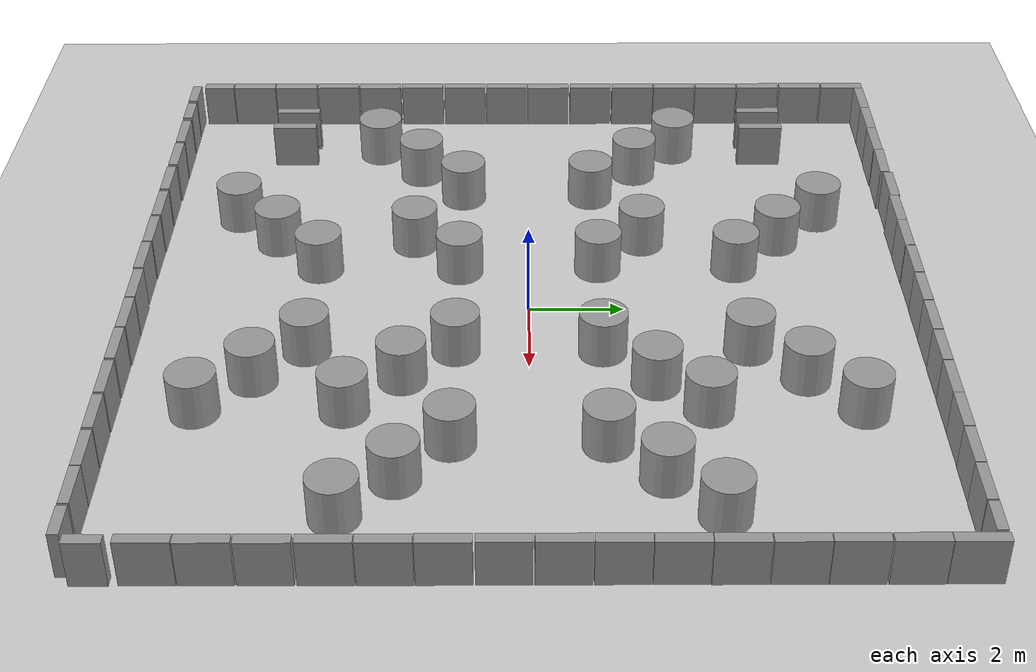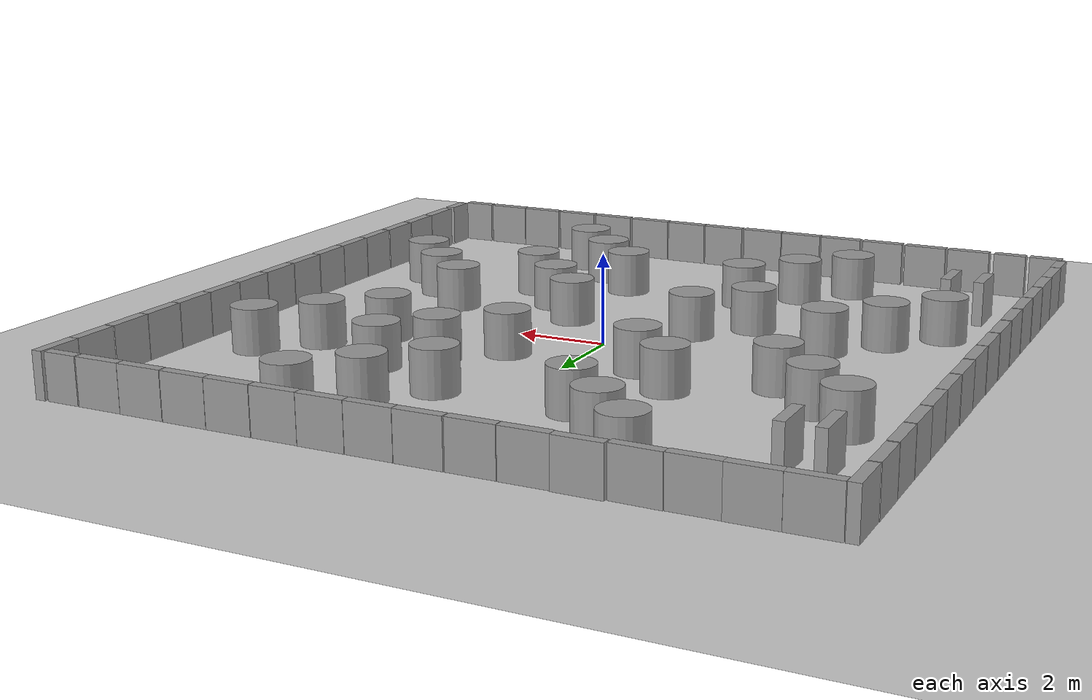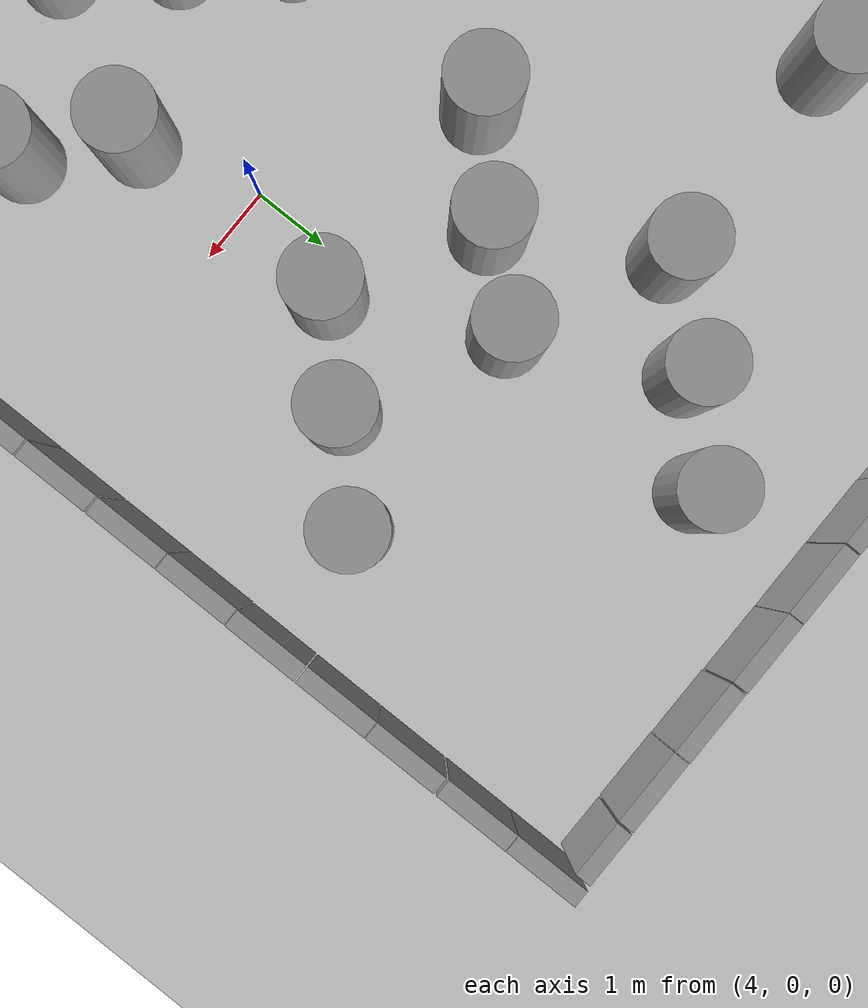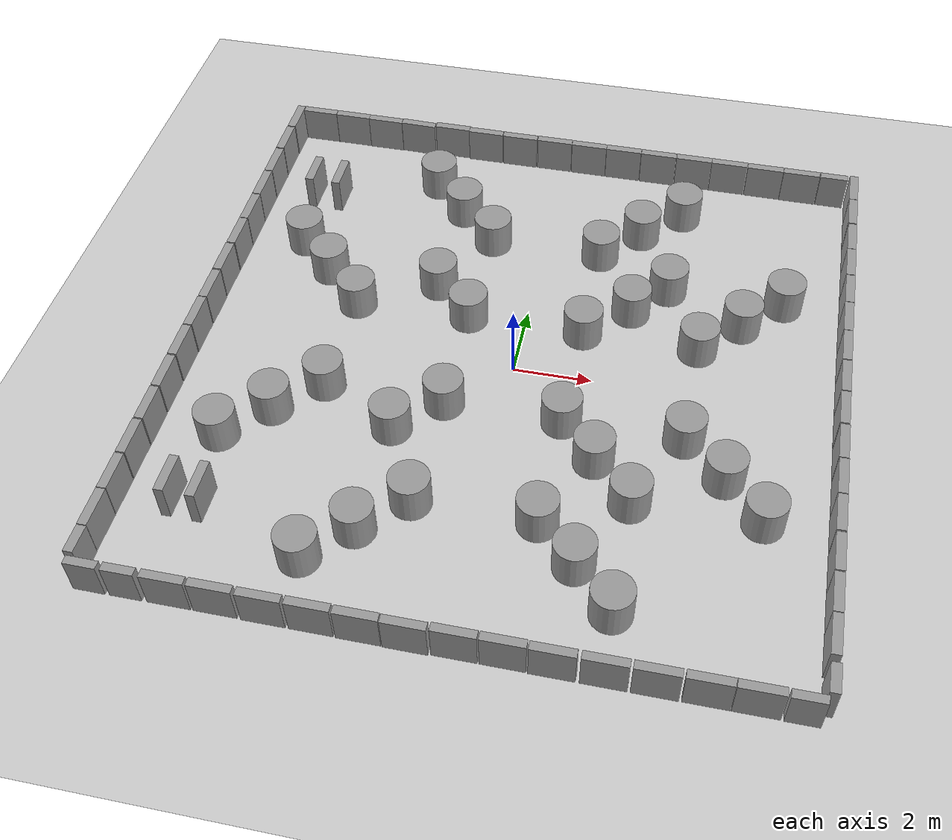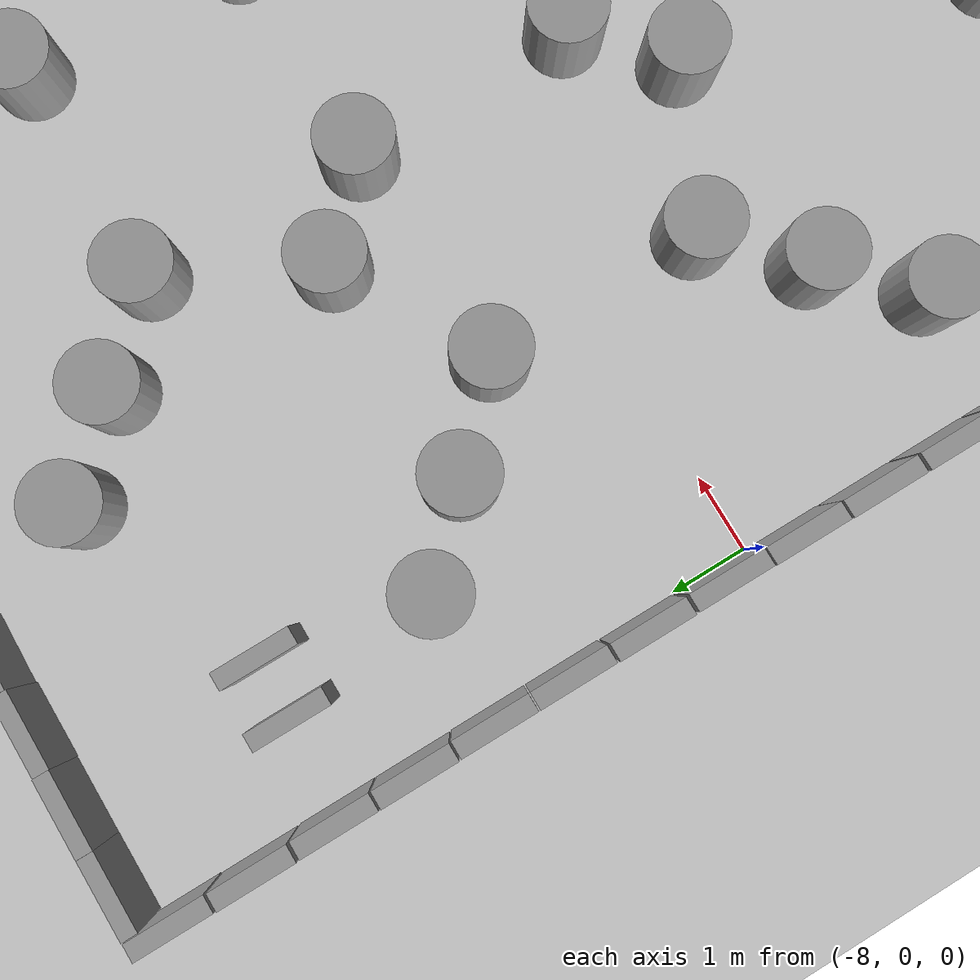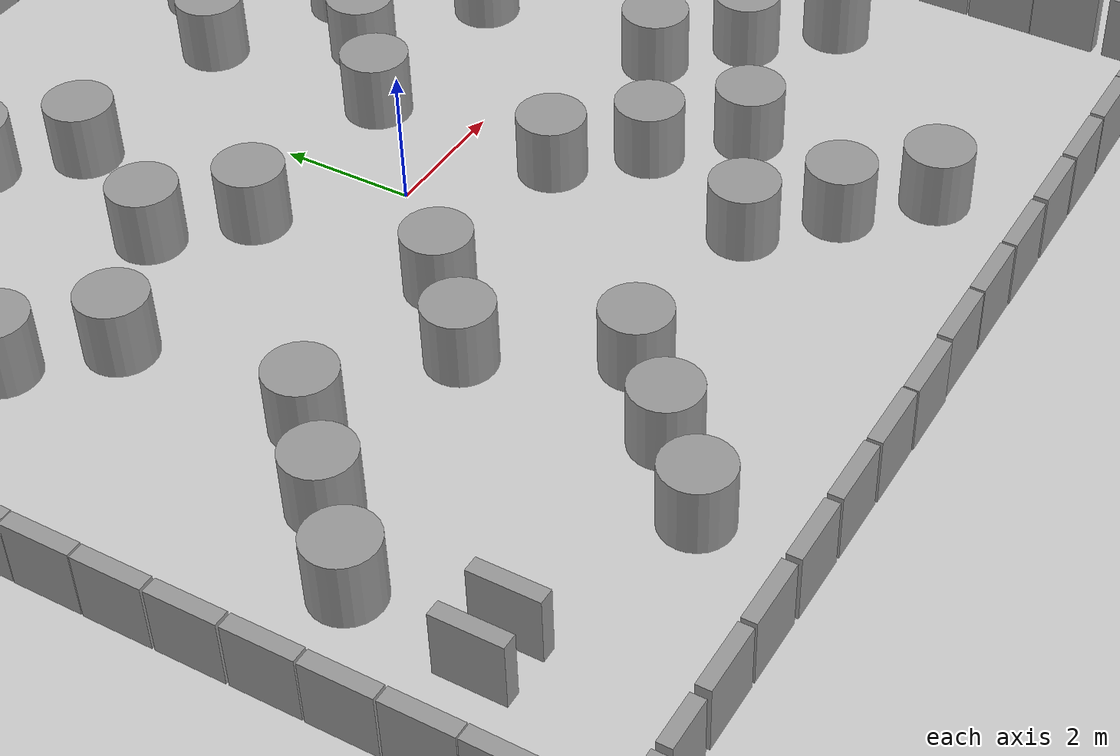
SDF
<sdf version="1.6">
 <world name="default">
  <light name="sun" type="directional">
   <pose>0 0 10 0 -0 0</pose>
   <diffuse>0.8 0.8 0.8 1</diffuse>
   <specular>0.1 0.1 0.1 1</specular>
   <attenuation>
    <range>1000</range>
    <constant>0.9</constant>
    <linear>0.01</linear>
    <quadratic>0.001</quadratic>
   </attenuation>
   <direction>-0.5 0.5 -1</direction>
  </light>
  <model name="ground_plane">
   <static>1</static>
   <static>1</static>
   <link name="link">
    <collision name="collision">
     <geometry><plane><normal>0 0 1</normal><size>100 100</size></plane></geometry>
     <surface><friction><ode><mu>100</mu><mu2>50</mu2></ode></friction></surface>
    </collision>
    <visual name="visual">
     <cast_shadows>0</cast_shadows>
     <geometry><plane><normal>0 0 1</normal><size>100 100</size></plane></geometry>
     <material>
      <script><uri>file://media/materials/scripts/gazebo.material</uri><name>Gazebo/Grey</name></script>
     </material>
    </visual>
   </link>
  </model>
  <gravity>0 0 -9.8</gravity>
  <magnetic_field>6e-06 2.3e-05 -4.2e-05</magnetic_field>
  <atmosphere type="adiabatic"/>
  <physics name="default_physics" default="0" type="ode">
   <max_step_size>0.001</max_step_size>
   <real_time_factor>1</real_time_factor>
   <real_time_update_rate>1000</real_time_update_rate>
  </physics>
  <scene><ambient>0.4 0.4 0.4 1</ambient><background>0.7 0.7 0.7 1</background><shadows>1</shadows></scene>
  <spherical_coordinates>
   <surface_model>EARTH_WGS84</surface_model>
   <latitude_deg>0</latitude_deg>
   <longitude_deg>0</longitude_deg>
   <elevation>0</elevation>
   <heading_deg>0</heading_deg>
  </spherical_coordinates>
  <audio><device>default</device></audio>
  <model name="unit_box_clone">
   <pose>-7.49845 8.11997 0.499999 1e-06 -2e-06 0.000235</pose>
   <link name="link">
    <inertial>
     <mass>1</mass>
     <inertia>
      <ixx>0.166667</ixx>
      <ixy>0</ixy>
      <ixz>0</ixz>
      <iyy>0.166667</iyy>
      <iyz>0</iyz>
      <izz>0.166667</izz>
     </inertia>
    </inertial>
    <collision name="collision"><geometry><box><size>1 0.210541 1</size></box></geometry></collision>
    <visual name="visual">
     <geometry><box><size>1 0.210541 1</size></box></geometry>
     <material>
      <script><name>Gazebo/Grey</name><uri>file://media/materials/scripts/gazebo.material</uri></script>
     </material>
    </visual>
   </link>
  </model>
  <model name="unit_box_clone_0">
   <pose>-6.4973 8.11987 0.499999 -1e-06 -2e-06 -0.002335</pose>
   <link name="link">
    <inertial>
     <mass>1</mass>
     <inertia>
      <ixx>0.166667</ixx>
      <ixy>0</ixy>
      <ixz>0</ixz>
      <iyy>0.166667</iyy>
      <iyz>0</iyz>
      <izz>0.166667</izz>
     </inertia>
    </inertial>
    <collision name="collision"><geometry><box><size>1 0.210541 1</size></box></geometry></collision>
    <visual name="visual">
     <geometry><box><size>1 0.210541 1</size></box></geometry>
     <material>
      <script><name>Gazebo/Grey</name><uri>file://media/materials/scripts/gazebo.material</uri></script>
     </material>
    </visual>
   </link>
  </model>
  <model name="unit_box_clone_1">
   <pose>-5.49732 8.10862 0.499999 -1e-06 -2e-06 -0.002327</pose>
   <link name="link">
    <inertial>
     <mass>1</mass>
     <inertia>
      <ixx>0.166667</ixx>
      <ixy>0</ixy>
      <ixz>0</ixz>
      <iyy>0.166667</iyy>
      <iyz>0</iyz>
      <izz>0.166667</izz>
     </inertia>
    </inertial>
    <collision name="collision"><geometry><box><size>1 0.210541 1</size></box></geometry></collision>
    <visual name="visual">
     <geometry><box><size>1 0.210541 1</size></box></geometry>
     <material>
      <script><name>Gazebo/Grey</name><uri>file://media/materials/scripts/gazebo.material</uri></script>
     </material>
    </visual>
   </link>
  </model>
  <model name="unit_box_clone_2">
   <pose>-4.49485 8.1107 0.499999 -1e-06 -2e-06 -0.026921</pose>
   <link name="link">
    <inertial>
     <mass>1</mass>
     <inertia>
      <ixx>0.166667</ixx>
      <ixy>0</ixy>
      <ixz>0</ixz>
      <iyy>0.166667</iyy>
      <iyz>0</iyz>
      <izz>0.166667</izz>
     </inertia>
    </inertial>
    <collision name="collision"><geometry><box><size>1 0.210541 1</size></box></geometry></collision>
    <visual name="visual">
     <geometry><box><size>1 0.210541 1</size></box></geometry>
     <material>
      <script><name>Gazebo/Grey</name><uri>file://media/materials/scripts/gazebo.material</uri></script>
     </material>
    </visual>
   </link>
  </model>
  <model name="unit_box_clone_3">
   <pose>-3.46835 8.15012 0.499999 1e-06 2e-06 -0.007855</pose>
   <link name="link">
    <inertial>
     <mass>1</mass>
     <inertia>
      <ixx>0.166667</ixx>
      <ixy>0</ixy>
      <ixz>0</ixz>
      <iyy>0.166667</iyy>
      <iyz>0</iyz>
      <izz>0.166667</izz>
     </inertia>
    </inertial>
    <collision name="collision"><geometry><box><size>1 0.210541 1</size></box></geometry></collision>
    <visual name="visual">
     <geometry><box><size>1 0.210541 1</size></box></geometry>
     <material>
      <script><name>Gazebo/Grey</name><uri>file://media/materials/scripts/gazebo.material</uri></script>
     </material>
    </visual>
   </link>
  </model>
  <model name="unit_box_clone_4">
   <pose>-2.46316 8.11866 0.499999 1e-06 -2e-06 0.000235</pose>
   <link name="link">
    <inertial>
     <mass>1</mass>
     <inertia>
      <ixx>0.166667</ixx>
      <ixy>0</ixy>
      <ixz>0</ixz>
      <iyy>0.166667</iyy>
      <iyz>0</iyz>
      <izz>0.166667</izz>
     </inertia>
    </inertial>
    <collision name="collision"><geometry><box><size>1 0.210541 1</size></box></geometry></collision>
    <visual name="visual">
     <geometry><box><size>1 0.210541 1</size></box></geometry>
     <material>
      <script><name>Gazebo/Grey</name><uri>file://media/materials/scripts/gazebo.material</uri></script>
     </material>
    </visual>
   </link>
  </model>
  <model name="unit_box_clone_5">
   <pose>-1.44425 8.112 0.499999 1e-06 -2e-06 0.000235</pose>
   <link name="link">
    <inertial>
     <mass>1</mass>
     <inertia>
      <ixx>0.166667</ixx>
      <ixy>0</ixy>
      <ixz>0</ixz>
      <iyy>0.166667</iyy>
      <iyz>0</iyz>
      <izz>0.166667</izz>
     </inertia>
    </inertial>
    <collision name="collision"><geometry><box><size>1 0.210541 1</size></box></geometry></collision>
    <visual name="visual">
     <geometry><box><size>1 0.210541 1</size></box></geometry>
     <material>
      <script><name>Gazebo/Grey</name><uri>file://media/materials/scripts/gazebo.material</uri></script>
     </material>
    </visual>
   </link>
  </model>
  <model name="unit_box_clone_6">
   <pose>-0.418685 8.11865 0.499999 1e-06 -2e-06 0.000235</pose>
   <link name="link">
    <inertial>
     <mass>1</mass>
     <inertia>
      <ixx>0.166667</ixx>
      <ixy>0</ixy>
      <ixz>0</ixz>
      <iyy>0.166667</iyy>
      <iyz>0</iyz>
      <izz>0.166667</izz>
     </inertia>
    </inertial>
    <collision name="collision"><geometry><box><size>1 0.210541 1</size></box></geometry></collision>
    <visual name="visual">
     <geometry><box><size>1 0.210541 1</size></box></geometry>
     <material>
      <script><name>Gazebo/Grey</name><uri>file://media/materials/scripts/gazebo.material</uri></script>
     </material>
    </visual>
   </link>
  </model>
  <model name="unit_box_clone_7">
   <pose>0.592834 8.11152 0.499999 1e-06 -2e-06 0.000235</pose>
   <link name="link">
    <inertial>
     <mass>1</mass>
     <inertia>
      <ixx>0.166667</ixx>
      <ixy>0</ixy>
      <ixz>0</ixz>
      <iyy>0.166667</iyy>
      <iyz>0</iyz>
      <izz>0.166667</izz>
     </inertia>
    </inertial>
    <collision name="collision"><geometry><box><size>1 0.210541 1</size></box></geometry></collision>
    <visual name="visual">
     <geometry><box><size>1 0.210541 1</size></box></geometry>
     <material>
      <script><name>Gazebo/Grey</name><uri>file://media/materials/scripts/gazebo.material</uri></script>
     </material>
    </visual>
   </link>
  </model>
  <model name="unit_box_clone_8">
   <pose>1.60043 8.11003 0.499999 1e-06 -2e-06 0.000235</pose>
   <link name="link">
    <inertial>
     <mass>1</mass>
     <inertia>
      <ixx>0.166667</ixx>
      <ixy>0</ixy>
      <ixz>0</ixz>
      <iyy>0.166667</iyy>
      <iyz>0</iyz>
      <izz>0.166667</izz>
     </inertia>
    </inertial>
    <collision name="collision"><geometry><box><size>1 0.210541 1</size></box></geometry></collision>
    <visual name="visual">
     <geometry><box><size>1 0.210541 1</size></box></geometry>
     <material>
      <script><name>Gazebo/Grey</name><uri>file://media/materials/scripts/gazebo.material</uri></script>
     </material>
    </visual>
   </link>
  </model>
  <model name="unit_box_clone_9">
   <pose>2.60987 8.10284 0.499999 1e-06 -2e-06 0.000235</pose>
   <link name="link">
    <inertial>
     <mass>1</mass>
     <inertia>
      <ixx>0.166667</ixx>
      <ixy>0</ixy>
      <ixz>0</ixz>
      <iyy>0.166667</iyy>
      <iyz>0</iyz>
      <izz>0.166667</izz>
     </inertia>
    </inertial>
    <collision name="collision"><geometry><box><size>1 0.210541 1</size></box></geometry></collision>
    <visual name="visual">
     <geometry><box><size>1 0.210541 1</size></box></geometry>
     <material>
      <script><name>Gazebo/Grey</name><uri>file://media/materials/scripts/gazebo.material</uri></script>
     </material>
    </visual>
   </link>
  </model>
  <model name="unit_box_clone_10">
   <pose>3.62649 8.09925 0.499999 1e-06 -2e-06 0.000235</pose>
   <link name="link">
    <inertial>
     <mass>1</mass>
     <inertia>
      <ixx>0.166667</ixx>
      <ixy>0</ixy>
      <ixz>0</ixz>
      <iyy>0.166667</iyy>
      <iyz>0</iyz>
      <izz>0.166667</izz>
     </inertia>
    </inertial>
    <collision name="collision"><geometry><box><size>1 0.210541 1</size></box></geometry></collision>
    <visual name="visual">
     <geometry><box><size>1 0.210541 1</size></box></geometry>
     <material>
      <script><name>Gazebo/Grey</name><uri>file://media/materials/scripts/gazebo.material</uri></script>
     </material>
    </visual>
   </link>
  </model>
  <model name="unit_box_clone_11">
   <pose>4.6331 8.09522 0.5 0 -0 -0.003289</pose>
   <link name="link">
    <inertial>
     <mass>1</mass>
     <inertia>
      <ixx>0.166667</ixx>
      <ixy>0</ixy>
      <ixz>0</ixz>
      <iyy>0.166667</iyy>
      <iyz>0</iyz>
      <izz>0.166667</izz>
     </inertia>
    </inertial>
    <collision name="collision"><geometry><box><size>1 0.210541 1</size></box></geometry></collision>
    <visual name="visual">
     <geometry><box><size>1 0.210541 1</size></box></geometry>
     <material>
      <script><name>Gazebo/Grey</name><uri>file://media/materials/scripts/gazebo.material</uri></script>
     </material>
    </visual>
   </link>
  </model>
  <model name="unit_box_0_clone_0">
   <pose>8.11522 6.68458 0.5 0 0 -0.000279</pose>
   <link name="link">
    <inertial>
     <mass>1</mass>
     <inertia>
      <ixx>0.166667</ixx>
      <ixy>0</ixy>
      <ixz>0</ixz>
      <iyy>0.166667</iyy>
      <iyz>0</iyz>
      <izz>0.166667</izz>
     </inertia>
    </inertial>
    <collision name="collision"><geometry><box><size>0.230819 1 1</size></box></geometry></collision>
    <visual name="visual">
     <geometry><box><size>0.230819 1 1</size></box></geometry>
     <material>
      <script><name>Gazebo/Grey</name><uri>file://media/materials/scripts/gazebo.material</uri></script>
     </material>
    </visual>
   </link>
  </model>
  <model name="unit_box_0_clone_1">
   <pose>8.11915 5.6517 0.5 1e-06 1e-06 0.000116</pose>
   <link name="link">
    <inertial>
     <mass>1</mass>
     <inertia>
      <ixx>0.166667</ixx>
      <ixy>0</ixy>
      <ixz>0</ixz>
      <iyy>0.166667</iyy>
      <iyz>0</iyz>
      <izz>0.166667</izz>
     </inertia>
    </inertial>
    <collision name="collision"><geometry><box><size>0.230819 1 1</size></box></geometry></collision>
    <visual name="visual">
     <geometry><box><size>0.230819 1 1</size></box></geometry>
     <material>
      <script><name>Gazebo/Grey</name><uri>file://media/materials/scripts/gazebo.material</uri></script>
     </material>
    </visual>
   </link>
  </model>
  <model name="unit_box_0_clone_2">
   <pose>8.11914 4.64016 0.5 1e-06 1e-06 0.00021</pose>
   <link name="link">
    <inertial>
     <mass>1</mass>
     <inertia>
      <ixx>0.166667</ixx>
      <ixy>0</ixy>
      <ixz>0</ixz>
      <iyy>0.166667</iyy>
      <iyz>0</iyz>
      <izz>0.166667</izz>
     </inertia>
    </inertial>
    <collision name="collision"><geometry><box><size>0.230819 1 1</size></box></geometry></collision>
    <visual name="visual">
     <geometry><box><size>0.230819 1 1</size></box></geometry>
     <material>
      <script><name>Gazebo/Grey</name><uri>file://media/materials/scripts/gazebo.material</uri></script>
     </material>
    </visual>
   </link>
  </model>
  <model name="unit_box_0_clone_3">
   <pose>8.11914 3.62228 0.5 1e-06 1e-06 0.000191</pose>
   <link name="link">
    <inertial>
     <mass>1</mass>
     <inertia>
      <ixx>0.166667</ixx>
      <ixy>0</ixy>
      <ixz>0</ixz>
      <iyy>0.166667</iyy>
      <iyz>0</iyz>
      <izz>0.166667</izz>
     </inertia>
    </inertial>
    <collision name="collision"><geometry><box><size>0.230819 1 1</size></box></geometry></collision>
    <visual name="visual">
     <geometry><box><size>0.230819 1 1</size></box></geometry>
     <material>
      <script><name>Gazebo/Grey</name><uri>file://media/materials/scripts/gazebo.material</uri></script>
     </material>
    </visual>
   </link>
  </model>
  <model name="unit_box_0_clone_4">
   <pose>8.11332 2.61063 0.5 1e-06 1e-06 -0.001045</pose>
   <link name="link">
    <inertial>
     <mass>1</mass>
     <inertia>
      <ixx>0.166667</ixx>
      <ixy>0</ixy>
      <ixz>0</ixz>
      <iyy>0.166667</iyy>
      <iyz>0</iyz>
      <izz>0.166667</izz>
     </inertia>
    </inertial>
    <collision name="collision"><geometry><box><size>0.230819 1 1</size></box></geometry></collision>
    <visual name="visual">
     <geometry><box><size>0.230819 1 1</size></box></geometry>
     <material>
      <script><name>Gazebo/Grey</name><uri>file://media/materials/scripts/gazebo.material</uri></script>
     </material>
    </visual>
   </link>
  </model>
  <model name="unit_box_0_clone_5">
   <pose>8.11277 1.59919 0.5 1e-06 1e-06 0.000191</pose>
   <link name="link">
    <inertial>
     <mass>1</mass>
     <inertia>
      <ixx>0.166667</ixx>
      <ixy>0</ixy>
      <ixz>0</ixz>
      <iyy>0.166667</iyy>
      <iyz>0</iyz>
      <izz>0.166667</izz>
     </inertia>
    </inertial>
    <collision name="collision"><geometry><box><size>0.230819 1 1</size></box></geometry></collision>
    <visual name="visual">
     <geometry><box><size>0.230819 1 1</size></box></geometry>
     <material>
      <script><name>Gazebo/Grey</name><uri>file://media/materials/scripts/gazebo.material</uri></script>
     </material>
    </visual>
   </link>
  </model>
  <model name="unit_box_0_clone_6">
   <pose>8.11277 0.574937 0.5 1e-06 1e-06 0.000191</pose>
   <link name="link">
    <inertial>
     <mass>1</mass>
     <inertia>
      <ixx>0.166667</ixx>
      <ixy>0</ixy>
      <ixz>0</ixz>
      <iyy>0.166667</iyy>
      <iyz>0</iyz>
      <izz>0.166667</izz>
     </inertia>
    </inertial>
    <collision name="collision"><geometry><box><size>0.230819 1 1</size></box></geometry></collision>
    <visual name="visual">
     <geometry><box><size>0.230819 1 1</size></box></geometry>
     <material>
      <script><name>Gazebo/Grey</name><uri>file://media/materials/scripts/gazebo.material</uri></script>
     </material>
    </visual>
   </link>
  </model>
  <model name="unit_box_0_clone_7">
   <pose>8.11276 -0.449321 0.5 1e-06 1e-06 0.000191</pose>
   <link name="link">
    <inertial>
     <mass>1</mass>
     <inertia>
      <ixx>0.166667</ixx>
      <ixy>0</ixy>
      <ixz>0</ixz>
      <iyy>0.166667</iyy>
      <iyz>0</iyz>
      <izz>0.166667</izz>
     </inertia>
    </inertial>
    <collision name="collision"><geometry><box><size>0.230819 1 1</size></box></geometry></collision>
    <visual name="visual">
     <geometry><box><size>0.230819 1 1</size></box></geometry>
     <material>
      <script><name>Gazebo/Grey</name><uri>file://media/materials/scripts/gazebo.material</uri></script>
     </material>
    </visual>
   </link>
  </model>
  <model name="unit_box_0_clone_8">
   <pose>8.11912 -1.48629 0.5 1e-06 1e-06 0.000191</pose>
   <link name="link">
    <inertial>
     <mass>1</mass>
     <inertia>
      <ixx>0.166667</ixx>
      <ixy>0</ixy>
      <ixz>0</ixz>
      <iyy>0.166667</iyy>
      <iyz>0</iyz>
      <izz>0.166667</izz>
     </inertia>
    </inertial>
    <collision name="collision"><geometry><box><size>0.230819 1 1</size></box></geometry></collision>
    <visual name="visual">
     <geometry><box><size>0.230819 1 1</size></box></geometry>
     <material>
      <script><name>Gazebo/Grey</name><uri>file://media/materials/scripts/gazebo.material</uri></script>
     </material>
    </visual>
   </link>
  </model>
  <model name="unit_box_0_clone_9">
   <pose>8.12548 -2.5042 0.5 1e-06 1e-06 0.000191</pose>
   <link name="link">
    <inertial>
     <mass>1</mass>
     <inertia>
      <ixx>0.166667</ixx>
      <ixy>0</ixy>
      <ixz>0</ixz>
      <iyy>0.166667</iyy>
      <iyz>0</iyz>
      <izz>0.166667</izz>
     </inertia>
    </inertial>
    <collision name="collision"><geometry><box><size>0.230819 1 1</size></box></geometry></collision>
    <visual name="visual">
     <geometry><box><size>0.230819 1 1</size></box></geometry>
     <material>
      <script><name>Gazebo/Grey</name><uri>file://media/materials/scripts/gazebo.material</uri></script>
     </material>
    </visual>
   </link>
  </model>
  <model name="unit_box_0_clone_10">
   <pose>8.12331 -3.52223 0.5 1e-06 1e-06 0.000191</pose>
   <link name="link">
    <inertial>
     <mass>1</mass>
     <inertia>
      <ixx>0.166667</ixx>
      <ixy>0</ixy>
      <ixz>0</ixz>
      <iyy>0.166667</iyy>
      <iyz>0</iyz>
      <izz>0.166667</izz>
     </inertia>
    </inertial>
    <collision name="collision"><geometry><box><size>0.230819 1 1</size></box></geometry></collision>
    <visual name="visual">
     <geometry><box><size>0.230819 1 1</size></box></geometry>
     <material>
      <script><name>Gazebo/Grey</name><uri>file://media/materials/scripts/gazebo.material</uri></script>
     </material>
    </visual>
   </link>
  </model>
  <model name="unit_box_0_clone_11">
   <pose>8.1233 -4.56316 0.5 1e-06 1e-06 0.000191</pose>
   <link name="link">
    <inertial>
     <mass>1</mass>
     <inertia>
      <ixx>0.166667</ixx>
      <ixy>0</ixy>
      <ixz>0</ixz>
      <iyy>0.166667</iyy>
      <iyz>0</iyz>
      <izz>0.166667</izz>
     </inertia>
    </inertial>
    <collision name="collision"><geometry><box><size>0.230819 1 1</size></box></geometry></collision>
    <visual name="visual">
     <geometry><box><size>0.230819 1 1</size></box></geometry>
     <material>
      <script><name>Gazebo/Grey</name><uri>file://media/materials/scripts/gazebo.material</uri></script>
     </material>
    </visual>
   </link>
  </model>
  <model name="unit_box_0_clone_12">
   <pose>8.11815 -5.59377 0.5 1e-06 1e-06 0.000191</pose>
   <link name="link">
    <inertial>
     <mass>1</mass>
     <inertia>
      <ixx>0.166667</ixx>
      <ixy>0</ixy>
      <ixz>0</ixz>
      <iyy>0.166667</iyy>
      <iyz>0</iyz>
      <izz>0.166667</izz>
     </inertia>
    </inertial>
    <collision name="collision"><geometry><box><size>0.230819 1 1</size></box></geometry></collision>
    <visual name="visual">
     <geometry><box><size>0.230819 1 1</size></box></geometry>
     <material>
      <script><name>Gazebo/Grey</name><uri>file://media/materials/scripts/gazebo.material</uri></script>
     </material>
    </visual>
   </link>
  </model>
  <model name="unit_box_0_clone_13">
   <pose>8.11333 -6.60776 0.5 1e-06 1e-06 -0.00543</pose>
   <link name="link">
    <inertial>
     <mass>1</mass>
     <inertia>
      <ixx>0.166667</ixx>
      <ixy>0</ixy>
      <ixz>0</ixz>
      <iyy>0.166667</iyy>
      <iyz>0</iyz>
      <izz>0.166667</izz>
     </inertia>
    </inertial>
    <collision name="collision"><geometry><box><size>0.230819 1 1</size></box></geometry></collision>
    <visual name="visual">
     <geometry><box><size>0.230819 1 1</size></box></geometry>
     <material>
      <script><name>Gazebo/Grey</name><uri>file://media/materials/scripts/gazebo.material</uri></script>
     </material>
    </visual>
   </link>
  </model>
  <model name="unit_box_clone_15_clone_0">
   <pose>6.71207 -8.13107 0.499999 1e-06 -2e-06 0.000235</pose>
   <link name="link">
    <inertial>
     <mass>1</mass>
     <inertia>
      <ixx>0.166667</ixx>
      <ixy>0</ixy>
      <ixz>0</ixz>
      <iyy>0.166667</iyy>
      <iyz>0</iyz>
      <izz>0.166667</izz>
     </inertia>
    </inertial>
    <collision name="collision"><geometry><box><size>1 0.210541 1</size></box></geometry></collision>
    <visual name="visual">
     <geometry><box><size>1 0.210541 1</size></box></geometry>
     <material>
      <script><name>Gazebo/Grey</name><uri>file://media/materials/scripts/gazebo.material</uri></script>
     </material>
    </visual>
   </link>
  </model>
  <model name="unit_box_clone_15_clone_1">
   <pose>5.69715 -8.13106 0.499999 1e-06 -2e-06 0.000235</pose>
   <link name="link">
    <inertial>
     <mass>1</mass>
     <inertia>
      <ixx>0.166667</ixx>
      <ixy>0</ixy>
      <ixz>0</ixz>
      <iyy>0.166667</iyy>
      <iyz>0</iyz>
      <izz>0.166667</izz>
     </inertia>
    </inertial>
    <collision name="collision"><geometry><box><size>1 0.210541 1</size></box></geometry></collision>
    <visual name="visual">
     <geometry><box><size>1 0.210541 1</size></box></geometry>
     <material>
      <script><name>Gazebo/Grey</name><uri>file://media/materials/scripts/gazebo.material</uri></script>
     </material>
    </visual>
   </link>
  </model>
  <model name="unit_box_clone_15_clone_2">
   <pose>4.63881 -8.13724 0.499999 1e-06 -2e-06 0.000235</pose>
   <link name="link">
    <inertial>
     <mass>1</mass>
     <inertia>
      <ixx>0.166667</ixx>
      <ixy>0</ixy>
      <ixz>0</ixz>
      <iyy>0.166667</iyy>
      <iyz>0</iyz>
      <izz>0.166667</izz>
     </inertia>
    </inertial>
    <collision name="collision"><geometry><box><size>1 0.210541 1</size></box></geometry></collision>
    <visual name="visual">
     <geometry><box><size>1 0.210541 1</size></box></geometry>
     <material>
      <script><name>Gazebo/Grey</name><uri>file://media/materials/scripts/gazebo.material</uri></script>
     </material>
    </visual>
   </link>
  </model>
  <model name="unit_box_clone_15_clone_3">
   <pose>3.57975 -8.13724 0.499999 1e-06 -2e-06 0.000235</pose>
   <link name="link">
    <inertial>
     <mass>1</mass>
     <inertia>
      <ixx>0.166667</ixx>
      <ixy>0</ixy>
      <ixz>0</ixz>
      <iyy>0.166667</iyy>
      <iyz>0</iyz>
      <izz>0.166667</izz>
     </inertia>
    </inertial>
    <collision name="collision"><geometry><box><size>1 0.210541 1</size></box></geometry></collision>
    <visual name="visual">
     <geometry><box><size>1 0.210541 1</size></box></geometry>
     <material>
      <script><name>Gazebo/Grey</name><uri>file://media/materials/scripts/gazebo.material</uri></script>
     </material>
    </visual>
   </link>
  </model>
  <model name="unit_box_clone_15_clone_4">
   <pose>2.49815 -8.13723 0.499999 1e-06 -2e-06 0.000235</pose>
   <link name="link">
    <inertial>
     <mass>1</mass>
     <inertia>
      <ixx>0.166667</ixx>
      <ixy>0</ixy>
      <ixz>0</ixz>
      <iyy>0.166667</iyy>
      <iyz>0</iyz>
      <izz>0.166667</izz>
     </inertia>
    </inertial>
    <collision name="collision"><geometry><box><size>1 0.210541 1</size></box></geometry></collision>
    <visual name="visual">
     <geometry><box><size>1 0.210541 1</size></box></geometry>
     <material>
      <script><name>Gazebo/Grey</name><uri>file://media/materials/scripts/gazebo.material</uri></script>
     </material>
    </visual>
   </link>
  </model>
  <model name="unit_box_clone_15_clone_5">
   <pose>1.46162 -8.12596 0.499999 1e-06 -2e-06 0.000235</pose>
   <link name="link">
    <inertial>
     <mass>1</mass>
     <inertia>
      <ixx>0.166667</ixx>
      <ixy>0</ixy>
      <ixz>0</ixz>
      <iyy>0.166667</iyy>
      <iyz>0</iyz>
      <izz>0.166667</izz>
     </inertia>
    </inertial>
    <collision name="collision"><geometry><box><size>1 0.210541 1</size></box></geometry></collision>
    <visual name="visual">
     <geometry><box><size>1 0.210541 1</size></box></geometry>
     <material>
      <script><name>Gazebo/Grey</name><uri>file://media/materials/scripts/gazebo.material</uri></script>
     </material>
    </visual>
   </link>
  </model>
  <model name="unit_box_clone_15_clone_6">
   <pose>0.425087 -8.12595 0.499999 1e-06 -2e-06 0.000235</pose>
   <link name="link">
    <inertial>
     <mass>1</mass>
     <inertia>
      <ixx>0.166667</ixx>
      <ixy>0</ixy>
      <ixz>0</ixz>
      <iyy>0.166667</iyy>
      <iyz>0</iyz>
      <izz>0.166667</izz>
     </inertia>
    </inertial>
    <collision name="collision"><geometry><box><size>1 0.210541 1</size></box></geometry></collision>
    <visual name="visual">
     <geometry><box><size>1 0.210541 1</size></box></geometry>
     <material>
      <script><name>Gazebo/Grey</name><uri>file://media/materials/scripts/gazebo.material</uri></script>
     </material>
    </visual>
   </link>
  </model>
  <model name="unit_box_clone_15_clone_7">
   <pose>-0.633975 -8.1485 0.499999 1e-06 -2e-06 0.000235</pose>
   <link name="link">
    <inertial>
     <mass>1</mass>
     <inertia>
      <ixx>0.166667</ixx>
      <ixy>0</ixy>
      <ixz>0</ixz>
      <iyy>0.166667</iyy>
      <iyz>0</iyz>
      <izz>0.166667</izz>
     </inertia>
    </inertial>
    <collision name="collision"><geometry><box><size>1 0.210541 1</size></box></geometry></collision>
    <visual name="visual">
     <geometry><box><size>1 0.210541 1</size></box></geometry>
     <material>
      <script><name>Gazebo/Grey</name><uri>file://media/materials/scripts/gazebo.material</uri></script>
     </material>
    </visual>
   </link>
  </model>
  <model name="unit_box_clone_15_clone_8">
   <pose>-1.65923 -8.13722 0.499999 1e-06 -2e-06 0.000235</pose>
   <link name="link">
    <inertial>
     <mass>1</mass>
     <inertia>
      <ixx>0.166667</ixx>
      <ixy>0</ixy>
      <ixz>0</ixz>
      <iyy>0.166667</iyy>
      <iyz>0</iyz>
      <izz>0.166667</izz>
     </inertia>
    </inertial>
    <collision name="collision"><geometry><box><size>1 0.210541 1</size></box></geometry></collision>
    <visual name="visual">
     <geometry><box><size>1 0.210541 1</size></box></geometry>
     <material>
      <script><name>Gazebo/Grey</name><uri>file://media/materials/scripts/gazebo.material</uri></script>
     </material>
    </visual>
   </link>
  </model>
  <model name="unit_box_clone_15_clone_9">
   <pose>-2.70703 -8.12597 0.499999 1e-06 -2e-06 0.000235</pose>
   <link name="link">
    <inertial>
     <mass>1</mass>
     <inertia>
      <ixx>0.166667</ixx>
      <ixy>0</ixy>
      <ixz>0</ixz>
      <iyy>0.166667</iyy>
      <iyz>0</iyz>
      <izz>0.166667</izz>
     </inertia>
    </inertial>
    <collision name="collision"><geometry><box><size>1 0.210541 1</size></box></geometry></collision>
    <visual name="visual">
     <geometry><box><size>1 0.210541 1</size></box></geometry>
     <material>
      <script><name>Gazebo/Grey</name><uri>file://media/materials/scripts/gazebo.material</uri></script>
     </material>
    </visual>
   </link>
  </model>
  <model name="unit_box_clone_15_clone_10">
   <pose>-3.77736 -8.12596 0.499999 1e-06 -2e-06 0.000235</pose>
   <link name="link">
    <inertial>
     <mass>1</mass>
     <inertia>
      <ixx>0.166667</ixx>
      <ixy>0</ixy>
      <ixz>0</ixz>
      <iyy>0.166667</iyy>
      <iyz>0</iyz>
      <izz>0.166667</izz>
     </inertia>
    </inertial>
    <collision name="collision"><geometry><box><size>1 0.210541 1</size></box></geometry></collision>
    <visual name="visual">
     <geometry><box><size>1 0.210541 1</size></box></geometry>
     <material>
      <script><name>Gazebo/Grey</name><uri>file://media/materials/scripts/gazebo.material</uri></script>
     </material>
    </visual>
   </link>
  </model>
  <model name="unit_box_clone_15_clone_11">
   <pose>-4.85896 -8.1147 0.499999 1e-06 -2e-06 0.000235</pose>
   <link name="link">
    <inertial>
     <mass>1</mass>
     <inertia>
      <ixx>0.166667</ixx>
      <ixy>0</ixy>
      <ixz>0</ixz>
      <iyy>0.166667</iyy>
      <iyz>0</iyz>
      <izz>0.166667</izz>
     </inertia>
    </inertial>
    <collision name="collision"><geometry><box><size>1 0.210541 1</size></box></geometry></collision>
    <visual name="visual">
     <geometry><box><size>1 0.210541 1</size></box></geometry>
     <material>
      <script><name>Gazebo/Grey</name><uri>file://media/materials/scripts/gazebo.material</uri></script>
     </material>
    </visual>
   </link>
  </model>
  <model name="unit_box_clone_15_clone_12">
   <pose>-5.91802 -8.11469 0.499999 1e-06 -2e-06 0.000235</pose>
   <link name="link">
    <inertial>
     <mass>1</mass>
     <inertia>
      <ixx>0.166667</ixx>
      <ixy>0</ixy>
      <ixz>0</ixz>
      <iyy>0.166667</iyy>
      <iyz>0</iyz>
      <izz>0.166667</izz>
     </inertia>
    </inertial>
    <collision name="collision"><geometry><box><size>1 0.210541 1</size></box></geometry></collision>
    <visual name="visual">
     <geometry><box><size>1 0.210541 1</size></box></geometry>
     <material>
      <script><name>Gazebo/Grey</name><uri>file://media/materials/scripts/gazebo.material</uri></script>
     </material>
    </visual>
   </link>
  </model>
  <model name="unit_box_0_clone_4_clone">
   <pose>-8.12647 7.71769 0.5 1e-06 1e-06 0.000191</pose>
   <link name="link">
    <inertial>
     <mass>1</mass>
     <inertia>
      <ixx>0.166667</ixx>
      <ixy>0</ixy>
      <ixz>0</ixz>
      <iyy>0.166667</iyy>
      <iyz>0</iyz>
      <izz>0.166667</izz>
     </inertia>
    </inertial>
    <collision name="collision"><geometry><box><size>0.230819 1 1</size></box></geometry></collision>
    <visual name="visual">
     <geometry><box><size>0.230819 1 1</size></box></geometry>
     <material>
      <script><name>Gazebo/Grey</name><uri>file://media/materials/scripts/gazebo.material</uri></script>
     </material>
    </visual>
   </link>
  </model>
  <model name="unit_box_0_clone_4_clone_0">
   <pose>-8.13281 6.68715 0.5 1e-06 1e-06 0.000191</pose>
   <link name="link">
    <inertial>
     <mass>1</mass>
     <inertia>
      <ixx>0.166667</ixx>
      <ixy>0</ixy>
      <ixz>0</ixz>
      <iyy>0.166667</iyy>
      <iyz>0</iyz>
      <izz>0.166667</izz>
     </inertia>
    </inertial>
    <collision name="collision"><geometry><box><size>0.230819 1 1</size></box></geometry></collision>
    <visual name="visual">
     <geometry><box><size>0.230819 1 1</size></box></geometry>
     <material>
      <script><name>Gazebo/Grey</name><uri>file://media/materials/scripts/gazebo.material</uri></script>
     </material>
    </visual>
   </link>
  </model>
  <model name="unit_box_0_clone_4_clone_1">
   <pose>-8.12606 5.64722 0.5 1e-06 1e-06 0.000191</pose>
   <link name="link">
    <inertial>
     <mass>1</mass>
     <inertia>
      <ixx>0.166667</ixx>
      <ixy>0</ixy>
      <ixz>0</ixz>
      <iyy>0.166667</iyy>
      <iyz>0</iyz>
      <izz>0.166667</izz>
     </inertia>
    </inertial>
    <collision name="collision"><geometry><box><size>0.230819 1 1</size></box></geometry></collision>
    <visual name="visual">
     <geometry><box><size>0.230819 1 1</size></box></geometry>
     <material>
      <script><name>Gazebo/Grey</name><uri>file://media/materials/scripts/gazebo.material</uri></script>
     </material>
    </visual>
   </link>
  </model>
  <model name="unit_box_0_clone_4_clone_2">
   <pose>-8.12607 4.6208 0.5 1e-06 1e-06 0.000191</pose>
   <link name="link">
    <inertial>
     <mass>1</mass>
     <inertia>
      <ixx>0.166667</ixx>
      <ixy>0</ixy>
      <ixz>0</ixz>
      <iyy>0.166667</iyy>
      <iyz>0</iyz>
      <izz>0.166667</izz>
     </inertia>
    </inertial>
    <collision name="collision"><geometry><box><size>0.230819 1 1</size></box></geometry></collision>
    <visual name="visual">
     <geometry><box><size>0.230819 1 1</size></box></geometry>
     <material>
      <script><name>Gazebo/Grey</name><uri>file://media/materials/scripts/gazebo.material</uri></script>
     </material>
    </visual>
   </link>
  </model>
  <model name="unit_box_0_clone_4_clone_3">
   <pose>-8.11932 3.59437 0.5 1e-06 1e-06 0.000191</pose>
   <link name="link">
    <inertial>
     <mass>1</mass>
     <inertia>
      <ixx>0.166667</ixx>
      <ixy>0</ixy>
      <ixz>0</ixz>
      <iyy>0.166667</iyy>
      <iyz>0</iyz>
      <izz>0.166667</izz>
     </inertia>
    </inertial>
    <collision name="collision"><geometry><box><size>0.230819 1 1</size></box></geometry></collision>
    <visual name="visual">
     <geometry><box><size>0.230819 1 1</size></box></geometry>
     <material>
      <script><name>Gazebo/Grey</name><uri>file://media/materials/scripts/gazebo.material</uri></script>
     </material>
    </visual>
   </link>
  </model>
  <model name="unit_box_0_clone_4_clone_4">
   <pose>-8.11932 2.57471 0.5 1e-06 1e-06 0.000191</pose>
   <link name="link">
    <inertial>
     <mass>1</mass>
     <inertia>
      <ixx>0.166667</ixx>
      <ixy>0</ixy>
      <ixz>0</ixz>
      <iyy>0.166667</iyy>
      <iyz>0</iyz>
      <izz>0.166667</izz>
     </inertia>
    </inertial>
    <collision name="collision"><geometry><box><size>0.230819 1 1</size></box></geometry></collision>
    <visual name="visual">
     <geometry><box><size>0.230819 1 1</size></box></geometry>
     <material>
      <script><name>Gazebo/Grey</name><uri>file://media/materials/scripts/gazebo.material</uri></script>
     </material>
    </visual>
   </link>
  </model>
  <model name="unit_box_0_clone_4_clone_5">
   <pose>-8.12608 1.54157 0.5 1e-06 1e-06 0.000191</pose>
   <link name="link">
    <inertial>
     <mass>1</mass>
     <inertia>
      <ixx>0.166667</ixx>
      <ixy>0</ixy>
      <ixz>0</ixz>
      <iyy>0.166667</iyy>
      <iyz>0</iyz>
      <izz>0.166667</izz>
     </inertia>
    </inertial>
    <collision name="collision"><geometry><box><size>0.230819 1 1</size></box></geometry></collision>
    <visual name="visual">
     <geometry><box><size>0.230819 1 1</size></box></geometry>
     <material>
      <script><name>Gazebo/Grey</name><uri>file://media/materials/scripts/gazebo.material</uri></script>
     </material>
    </visual>
   </link>
  </model>
  <model name="unit_box_0_clone_4_clone_6">
   <pose>-8.11933 0.501629 0.5 1e-06 1e-06 0.000191</pose>
   <link name="link">
    <inertial>
     <mass>1</mass>
     <inertia>
      <ixx>0.166667</ixx>
      <ixy>0</ixy>
      <ixz>0</ixz>
      <iyy>0.166667</iyy>
      <iyz>0</iyz>
      <izz>0.166667</izz>
     </inertia>
    </inertial>
    <collision name="collision"><geometry><box><size>0.230819 1 1</size></box></geometry></collision>
    <visual name="visual">
     <geometry><box><size>0.230819 1 1</size></box></geometry>
     <material>
      <script><name>Gazebo/Grey</name><uri>file://media/materials/scripts/gazebo.material</uri></script>
     </material>
    </visual>
   </link>
  </model>
  <model name="unit_box_0_clone_4_clone_7">
   <pose>-8.12609 -0.518035 0.5 1e-06 1e-06 0.000191</pose>
   <link name="link">
    <inertial>
     <mass>1</mass>
     <inertia>
      <ixx>0.166667</ixx>
      <ixy>0</ixy>
      <ixz>0</ixz>
      <iyy>0.166667</iyy>
      <iyz>0</iyz>
      <izz>0.166667</izz>
     </inertia>
    </inertial>
    <collision name="collision"><geometry><box><size>0.230819 1 1</size></box></geometry></collision>
    <visual name="visual">
     <geometry><box><size>0.230819 1 1</size></box></geometry>
     <material>
      <script><name>Gazebo/Grey</name><uri>file://media/materials/scripts/gazebo.material</uri></script>
     </material>
    </visual>
   </link>
  </model>
  <model name="unit_box_0_clone_4_clone_8">
   <pose>-8.13284 -1.54445 0.5 1e-06 1e-06 0.000191</pose>
   <link name="link">
    <inertial>
     <mass>1</mass>
     <inertia>
      <ixx>0.166667</ixx>
      <ixy>0</ixy>
      <ixz>0</ixz>
      <iyy>0.166667</iyy>
      <iyz>0</iyz>
      <izz>0.166667</izz>
     </inertia>
    </inertial>
    <collision name="collision"><geometry><box><size>0.230819 1 1</size></box></geometry></collision>
    <visual name="visual">
     <geometry><box><size>0.230819 1 1</size></box></geometry>
     <material>
      <script><name>Gazebo/Grey</name><uri>file://media/materials/scripts/gazebo.material</uri></script>
     </material>
    </visual>
   </link>
  </model>
  <model name="unit_box_0_clone_4_clone_9">
   <pose>-8.13285 -2.58439 0.5 1e-06 1e-06 0.000191</pose>
   <link name="link">
    <inertial>
     <mass>1</mass>
     <inertia>
      <ixx>0.166667</ixx>
      <ixy>0</ixy>
      <ixz>0</ixz>
      <iyy>0.166667</iyy>
      <iyz>0</iyz>
      <izz>0.166667</izz>
     </inertia>
    </inertial>
    <collision name="collision"><geometry><box><size>0.230819 1 1</size></box></geometry></collision>
    <visual name="visual">
     <geometry><box><size>0.230819 1 1</size></box></geometry>
     <material>
      <script><name>Gazebo/Grey</name><uri>file://media/materials/scripts/gazebo.material</uri></script>
     </material>
    </visual>
   </link>
  </model>
  <model name="unit_box_0_clone_4_clone_10">
   <pose>-8.13285 -3.62431 0.5 1e-06 1e-06 0.000191</pose>
   <link name="link">
    <inertial>
     <mass>1</mass>
     <inertia>
      <ixx>0.166667</ixx>
      <ixy>0</ixy>
      <ixz>0</ixz>
      <iyy>0.166667</iyy>
      <iyz>0</iyz>
      <izz>0.166667</izz>
     </inertia>
    </inertial>
    <collision name="collision"><geometry><box><size>0.230819 1 1</size></box></geometry></collision>
    <visual name="visual">
     <geometry><box><size>0.230819 1 1</size></box></geometry>
     <material>
      <script><name>Gazebo/Grey</name><uri>file://media/materials/scripts/gazebo.material</uri></script>
     </material>
    </visual>
   </link>
  </model>
  <model name="unit_box_0_clone_4_clone_11">
   <pose>-8.1396 -4.65747 0.5 1e-06 1e-06 0.000191</pose>
   <link name="link">
    <inertial>
     <mass>1</mass>
     <inertia>
      <ixx>0.166667</ixx>
      <ixy>0</ixy>
      <ixz>0</ixz>
      <iyy>0.166667</iyy>
      <iyz>0</iyz>
      <izz>0.166667</izz>
     </inertia>
    </inertial>
    <collision name="collision"><geometry><box><size>0.230819 1 1</size></box></geometry></collision>
    <visual name="visual">
     <geometry><box><size>0.230819 1 1</size></box></geometry>
     <material>
      <script><name>Gazebo/Grey</name><uri>file://media/materials/scripts/gazebo.material</uri></script>
     </material>
    </visual>
   </link>
  </model>
  <model name="unit_box_0_clone_4_clone_12">
   <pose>-8.1396 -5.69064 0.5 1e-06 1e-06 0.000191</pose>
   <link name="link">
    <inertial>
     <mass>1</mass>
     <inertia>
      <ixx>0.166667</ixx>
      <ixy>0</ixy>
      <ixz>0</ixz>
      <iyy>0.166667</iyy>
      <iyz>0</iyz>
      <izz>0.166667</izz>
     </inertia>
    </inertial>
    <collision name="collision"><geometry><box><size>0.230819 1 1</size></box></geometry></collision>
    <visual name="visual">
     <geometry><box><size>0.230819 1 1</size></box></geometry>
     <material>
      <script><name>Gazebo/Grey</name><uri>file://media/materials/scripts/gazebo.material</uri></script>
     </material>
    </visual>
   </link>
  </model>
  <model name="unit_box_0_clone_4_clone_13">
   <pose>-8.14113 -6.70873 0.5 0 0 -0.008861</pose>
   <link name="link">
    <inertial>
     <mass>1</mass>
     <inertia>
      <ixx>0.166667</ixx>
      <ixy>0</ixy>
      <ixz>0</ixz>
      <iyy>0.166667</iyy>
      <iyz>0</iyz>
      <izz>0.166667</izz>
     </inertia>
    </inertial>
    <collision name="collision"><geometry><box><size>0.230819 1 1</size></box></geometry></collision>
    <visual name="visual">
     <geometry><box><size>0.230819 1 1</size></box></geometry>
     <material>
      <script><name>Gazebo/Grey</name><uri>file://media/materials/scripts/gazebo.material</uri></script>
     </material>
    </visual>
   </link>
  </model>
  <model name="unit_box_0_clone_0_clone">
   <pose>8.11438 7.69322 0.5 1e-06 1e-06 9.8e-05</pose>
   <link name="link">
    <inertial>
     <mass>1</mass>
     <inertia>
      <ixx>0.166667</ixx>
      <ixy>0</ixy>
      <ixz>0</ixz>
      <iyy>0.166667</iyy>
      <iyz>0</iyz>
      <izz>0.166667</izz>
     </inertia>
    </inertial>
    <collision name="collision"><geometry><box><size>0.230819 1 1</size></box></geometry></collision>
    <visual name="visual">
     <geometry><box><size>0.230819 1 1</size></box></geometry>
     <material>
      <script><name>Gazebo/Grey</name><uri>file://media/materials/scripts/gazebo.material</uri></script>
     </material>
    </visual>
   </link>
  </model>
  <model name="unit_box_clone_11_clone">
   <pose>5.6544 8.08358 0.499999 1e-06 2e-06 -0.003013</pose>
   <link name="link">
    <inertial>
     <mass>1</mass>
     <inertia>
      <ixx>0.166667</ixx>
      <ixy>0</ixy>
      <ixz>0</ixz>
      <iyy>0.166667</iyy>
      <iyz>0</iyz>
      <izz>0.166667</izz>
     </inertia>
    </inertial>
    <collision name="collision"><geometry><box><size>1 0.210541 1</size></box></geometry></collision>
    <visual name="visual">
     <geometry><box><size>1 0.210541 1</size></box></geometry>
     <material>
      <script><name>Gazebo/Grey</name><uri>file://media/materials/scripts/gazebo.material</uri></script>
     </material>
    </visual>
   </link>
  </model>
  <model name="unit_box_clone_11_clone_0">
   <pose>6.6644 8.07341 0.5 0 -0 -0.003211</pose>
   <link name="link">
    <inertial>
     <mass>1</mass>
     <inertia>
      <ixx>0.166667</ixx>
      <ixy>0</ixy>
      <ixz>0</ixz>
      <iyy>0.166667</iyy>
      <iyz>0</iyz>
      <izz>0.166667</izz>
     </inertia>
    </inertial>
    <collision name="collision"><geometry><box><size>1 0.210541 1</size></box></geometry></collision>
    <visual name="visual">
     <geometry><box><size>1 0.210541 1</size></box></geometry>
     <material>
      <script><name>Gazebo/Grey</name><uri>file://media/materials/scripts/gazebo.material</uri></script>
     </material>
    </visual>
   </link>
  </model>
  <model name="unit_box_clone_11_clone_1_clone">
   <pose>7.56438 8.07324 0.5 -1e-06 -1e-06 -0.004604</pose>
   <link name="link">
    <inertial>
     <mass>1</mass>
     <inertia>
      <ixx>0.166667</ixx>
      <ixy>0</ixy>
      <ixz>0</ixz>
      <iyy>0.166667</iyy>
      <iyz>0</iyz>
      <izz>0.166667</izz>
     </inertia>
    </inertial>
    <collision name="collision"><geometry><box><size>0.750223 0.210541 1</size></box></geometry></collision>
    <visual name="visual">
     <geometry><box><size>0.750223 0.210541 1</size></box></geometry>
     <material>
      <script><name>Gazebo/Grey</name><uri>file://media/materials/scripts/gazebo.material</uri></script>
     </material>
    </visual>
   </link>
  </model>
  <model name="unit_box_clone_11_clone_1_clone_0">
   <pose>-6.90881 -8.11956 0.499997 -2e-06 -8e-06 -0.000196</pose>
   <link name="link">
    <inertial>
     <mass>1</mass>
     <inertia>
      <ixx>0.166667</ixx>
      <ixy>0</ixy>
      <ixz>0</ixz>
      <iyy>0.166667</iyy>
      <iyz>0</iyz>
      <izz>0.166667</izz>
     </inertia>
    </inertial>
    <collision name="collision"><geometry><box><size>0.750223 0.210541 1</size></box></geometry></collision>
    <visual name="visual">
     <geometry><box><size>0.750223 0.210541 1</size></box></geometry>
     <material>
      <script><name>Gazebo/Grey</name><uri>file://media/materials/scripts/gazebo.material</uri></script>
     </material>
    </visual>
   </link>
  </model>
  <model name="unit_box_0_clone_4_clone_13_clone_clone">
   <pose>-8.13833 -7.57661 0.499997 7e-06 -2e-06 -0.014534</pose>
   <link name="link">
    <inertial>
     <mass>1</mass>
     <inertia>
      <ixx>0.166667</ixx>
      <ixy>0</ixy>
      <ixz>0</ixz>
      <iyy>0.166667</iyy>
      <iyz>0</iyz>
      <izz>0.166667</izz>
     </inertia>
    </inertial>
    <collision name="collision"><geometry><box><size>0.230819 0.700336 1</size></box></geometry></collision>
    <visual name="visual">
     <geometry><box><size>0.230819 0.700336 1</size></box></geometry>
     <material>
      <script><name>Gazebo/Grey</name><uri>file://media/materials/scripts/gazebo.material</uri></script>
     </material>
    </visual>
   </link>
  </model>
  <model name="unit_box_clone_11_clone_1_clone_0_clone">
   <pose>-7.75474 -8.12201 0.5 -0 1e-06 -0.00569</pose>
   <link name="link">
    <inertial>
     <mass>1</mass>
     <inertia>
      <ixx>0.166667</ixx>
      <ixy>0</ixy>
      <ixz>0</ixz>
      <iyy>0.166667</iyy>
      <iyz>0</iyz>
      <izz>0.166667</izz>
     </inertia>
    </inertial>
    <collision name="collision"><geometry><box><size>0.750223 0.210541 1</size></box></geometry></collision>
    <visual name="visual">
     <geometry><box><size>0.750223 0.210541 1</size></box></geometry>
     <material>
      <script><name>Gazebo/Grey</name><uri>file://media/materials/scripts/gazebo.material</uri></script>
     </material>
    </visual>
   </link>
  </model>
  <model name="unit_box_clone_11_clone_1_clone_2">
   <pose>7.64248 -8.13928 0.499997 -2e-06 7e-06 0.001332</pose>
   <link name="link">
    <inertial>
     <mass>1</mass>
     <inertia>
      <ixx>0.166667</ixx>
      <ixy>0</ixy>
      <ixz>0</ixz>
      <iyy>0.166667</iyy>
      <iyz>0</iyz>
      <izz>0.166667</izz>
     </inertia>
    </inertial>
    <collision name="collision"><geometry><box><size>0.750223 0.210541 1</size></box></geometry></collision>
    <visual name="visual">
     <geometry><box><size>0.750223 0.210541 1</size></box></geometry>
     <material>
      <script><name>Gazebo/Grey</name><uri>file://media/materials/scripts/gazebo.material</uri></script>
     </material>
    </visual>
   </link>
  </model>
  <model name="unit_box_0_clone_4_clone_13_clone_clone_clone">
   <pose>8.11858 -7.62155 0.499997 -7e-06 -1e-06 -0.005477</pose>
   <link name="link">
    <inertial>
     <mass>1</mass>
     <inertia>
      <ixx>0.166667</ixx>
      <ixy>0</ixy>
      <ixz>0</ixz>
      <iyy>0.166667</iyy>
      <iyz>0</iyz>
      <izz>0.166667</izz>
     </inertia>
    </inertial>
    <collision name="collision"><geometry><box><size>0.230819 0.700336 1</size></box></geometry></collision>
    <visual name="visual">
     <geometry><box><size>0.230819 0.700336 1</size></box></geometry>
     <material>
      <script><name>Gazebo/Grey</name><uri>file://media/materials/scripts/gazebo.material</uri></script>
     </material>
    </visual>
   </link>
  </model>
  <model name="unit_cylinder_clone">
   <pose>-1.49009 1.49927 0.499997 4e-06 2e-06 -0</pose>
   <link name="link">
    <inertial>
     <mass>1</mass>
     <inertia><ixx>0.145833</ixx><ixy>0</ixy><ixz>0</ixz><iyy>0.145833</iyy><iyz>0</iyz><izz>0.125</izz></inertia>
    </inertial>
    <collision name="collision">
     <geometry><cylinder><radius>0.5</radius><length>1</length></cylinder></geometry>
    </collision>
    <visual name="visual">
     <geometry><cylinder><radius>0.5</radius><length>1</length></cylinder></geometry>
     <material>
      <script><name>Gazebo/Grey</name><uri>file://media/materials/scripts/gazebo.material</uri></script>
     </material>
    </visual>
   </link>
  </model>
  <model name="unit_cylinder_clone_0">
   <pose>-2.53052 2.49544 0.499994 -4e-06 -3e-06 -0</pose>
   <link name="link">
    <inertial>
     <mass>1</mass>
     <inertia><ixx>0.145833</ixx><ixy>0</ixy><ixz>0</ixz><iyy>0.145833</iyy><iyz>0</iyz><izz>0.125</izz></inertia>
    </inertial>
    <collision name="collision">
     <geometry><cylinder><radius>0.5</radius><length>1</length></cylinder></geometry>
    </collision>
    <visual name="visual">
     <geometry><cylinder><radius>0.5</radius><length>1</length></cylinder></geometry>
     <material>
      <script><name>Gazebo/Grey</name><uri>file://media/materials/scripts/gazebo.material</uri></script>
     </material>
    </visual>
   </link>
  </model>
  <model name="unit_cylinder_clone_0_clone">
   <pose>1.52056 1.49925 0.499997 4e-06 3e-06 -0</pose>
   <link name="link">
    <inertial>
     <mass>1</mass>
     <inertia><ixx>0.145833</ixx><ixy>0</ixy><ixz>0</ixz><iyy>0.145833</iyy><iyz>0</iyz><izz>0.125</izz></inertia>
    </inertial>
    <collision name="collision">
     <geometry><cylinder><radius>0.5</radius><length>1</length></cylinder></geometry>
    </collision>
    <visual name="visual">
     <geometry><cylinder><radius>0.5</radius><length>1</length></cylinder></geometry>
     <material>
      <script><name>Gazebo/Grey</name><uri>file://media/materials/scripts/gazebo.material</uri></script>
     </material>
    </visual>
   </link>
  </model>
  <model name="unit_cylinder_clone_0_clone_0">
   <pose>2.62743 2.51755 0.499997 4e-06 3e-06 -0</pose>
   <link name="link">
    <inertial>
     <mass>1</mass>
     <inertia><ixx>0.145833</ixx><ixy>0</ixy><ixz>0</ixz><iyy>0.145833</iyy><iyz>0</iyz><izz>0.125</izz></inertia>
    </inertial>
    <collision name="collision">
     <geometry><cylinder><radius>0.5</radius><length>1</length></cylinder></geometry>
    </collision>
    <visual name="visual">
     <geometry><cylinder><radius>0.5</radius><length>1</length></cylinder></geometry>
     <material>
      <script><name>Gazebo/Grey</name><uri>file://media/materials/scripts/gazebo.material</uri></script>
     </material>
    </visual>
   </link>
  </model>
  <model name="unit_cylinder_clone_0_clone_1">
   <pose>1.49841 -1.48926 0.499997 4e-06 3e-06 -0</pose>
   <link name="link">
    <inertial>
     <mass>1</mass>
     <inertia><ixx>0.145833</ixx><ixy>0</ixy><ixz>0</ixz><iyy>0.145833</iyy><iyz>0</iyz><izz>0.125</izz></inertia>
    </inertial>
    <collision name="collision">
     <geometry><cylinder><radius>0.5</radius><length>1</length></cylinder></geometry>
    </collision>
    <visual name="visual">
     <geometry><cylinder><radius>0.5</radius><length>1</length></cylinder></geometry>
     <material>
      <script><name>Gazebo/Grey</name><uri>file://media/materials/scripts/gazebo.material</uri></script>
     </material>
    </visual>
   </link>
  </model>
  <model name="unit_cylinder_clone_0_clone_2">
   <pose>2.4503 -2.52971 0.499997 4e-06 4e-06 -0</pose>
   <link name="link">
    <inertial>
     <mass>1</mass>
     <inertia><ixx>0.145833</ixx><ixy>0</ixy><ixz>0</ixz><iyy>0.145833</iyy><iyz>0</iyz><izz>0.125</izz></inertia>
    </inertial>
    <collision name="collision">
     <geometry><cylinder><radius>0.5</radius><length>1</length></cylinder></geometry>
    </collision>
    <visual name="visual">
     <geometry><cylinder><radius>0.5</radius><length>1</length></cylinder></geometry>
     <material>
      <script><name>Gazebo/Grey</name><uri>file://media/materials/scripts/gazebo.material</uri></script>
     </material>
    </visual>
   </link>
  </model>
  <model name="unit_cylinder_clone_0_clone_3">
   <pose>-1.42369 -1.48925 0.499994 -4e-06 -4e-06 -0</pose>
   <link name="link">
    <inertial>
     <mass>1</mass>
     <inertia><ixx>0.145833</ixx><ixy>0</ixy><ixz>0</ixz><iyy>0.145833</iyy><iyz>0</iyz><izz>0.125</izz></inertia>
    </inertial>
    <collision name="collision">
     <geometry><cylinder><radius>0.5</radius><length>1</length></cylinder></geometry>
    </collision>
    <visual name="visual">
     <geometry><cylinder><radius>0.5</radius><length>1</length></cylinder></geometry>
     <material>
      <script><name>Gazebo/Grey</name><uri>file://media/materials/scripts/gazebo.material</uri></script>
     </material>
    </visual>
   </link>
  </model>
  <model name="unit_cylinder_clone_0_clone_4">
   <pose>-2.48628 -2.50755 0.499998 3e-06 4e-06 -0</pose>
   <link name="link">
    <inertial>
     <mass>1</mass>
     <inertia><ixx>0.145833</ixx><ixy>0</ixy><ixz>0</ixz><iyy>0.145833</iyy><iyz>0</iyz><izz>0.125</izz></inertia>
    </inertial>
    <collision name="collision">
     <geometry><cylinder><radius>0.5</radius><length>1</length></cylinder></geometry>
    </collision>
    <visual name="visual">
     <geometry><cylinder><radius>0.5</radius><length>1</length></cylinder></geometry>
     <material>
      <script><name>Gazebo/Grey</name><uri>file://media/materials/scripts/gazebo.material</uri></script>
     </material>
    </visual>
   </link>
  </model>
  <model name="unit_cylinder_clone_0_clone_5">
   <pose>-1.47717 4.46303 0.499998 3e-06 4e-06 -0</pose>
   <link name="link">
    <inertial>
     <mass>1</mass>
     <inertia><ixx>0.145833</ixx><ixy>0</ixy><ixz>0</ixz><iyy>0.145833</iyy><iyz>0</iyz><izz>0.125</izz></inertia>
    </inertial>
    <collision name="collision">
     <geometry><cylinder><radius>0.5</radius><length>1</length></cylinder></geometry>
    </collision>
    <visual name="visual">
     <geometry><cylinder><radius>0.5</radius><length>1</length></cylinder></geometry>
     <material>
      <script><name>Gazebo/Grey</name><uri>file://media/materials/scripts/gazebo.material</uri></script>
     </material>
    </visual>
   </link>
  </model>
  <model name="unit_cylinder_clone_0_clone_6">
   <pose>-2.50999 5.47973 0.499998 3e-06 4e-06 -0</pose>
   <link name="link">
    <inertial>
     <mass>1</mass>
     <inertia><ixx>0.145833</ixx><ixy>0</ixy><ixz>0</ixz><iyy>0.145833</iyy><iyz>0</iyz><izz>0.125</izz></inertia>
    </inertial>
    <collision name="collision">
     <geometry><cylinder><radius>0.5</radius><length>1</length></cylinder></geometry>
    </collision>
    <visual name="visual">
     <geometry><cylinder><radius>0.5</radius><length>1</length></cylinder></geometry>
     <material>
      <script><name>Gazebo/Grey</name><uri>file://media/materials/scripts/gazebo.material</uri></script>
     </material>
    </visual>
   </link>
  </model>
  <model name="unit_cylinder_clone_0_clone_7">
   <pose>-3.4944 6.51256 0.499996 4e-06 3e-06 -0</pose>
   <link name="link">
    <inertial>
     <mass>1</mass>
     <inertia><ixx>0.145833</ixx><ixy>0</ixy><ixz>0</ixz><iyy>0.145833</iyy><iyz>0</iyz><izz>0.125</izz></inertia>
    </inertial>
    <collision name="collision">
     <geometry><cylinder><radius>0.5</radius><length>1</length></cylinder></geometry>
    </collision>
    <visual name="visual">
     <geometry><cylinder><radius>0.5</radius><length>1</length></cylinder></geometry>
     <material>
      <script><name>Gazebo/Grey</name><uri>file://media/materials/scripts/gazebo.material</uri></script>
     </material>
    </visual>
   </link>
  </model>
  <model name="unit_cylinder_clone_0_clone_8">
   <pose>1.50835 4.46301 0.499994 -4e-06 -3e-06 -0</pose>
   <link name="link">
    <inertial>
     <mass>1</mass>
     <inertia><ixx>0.145833</ixx><ixy>0</ixy><ixz>0</ixz><iyy>0.145833</iyy><iyz>0</iyz><izz>0.125</izz></inertia>
    </inertial>
    <collision name="collision">
     <geometry><cylinder><radius>0.5</radius><length>1</length></cylinder></geometry>
    </collision>
    <visual name="visual">
     <geometry><cylinder><radius>0.5</radius><length>1</length></cylinder></geometry>
     <material>
      <script><name>Gazebo/Grey</name><uri>file://media/materials/scripts/gazebo.material</uri></script>
     </material>
    </visual>
   </link>
  </model>
  <model name="unit_cylinder_clone_0_clone_10">
   <pose>3.52561 6.51252 0.499992 -3e-06 2e-06 0</pose>
   <link name="link">
    <inertial>
     <mass>1</mass>
     <inertia><ixx>0.145833</ixx><ixy>0</ixy><ixz>0</ixz><iyy>0.145833</iyy><iyz>0</iyz><izz>0.125</izz></inertia>
    </inertial>
    <collision name="collision">
     <geometry><cylinder><radius>0.5</radius><length>1</length></cylinder></geometry>
    </collision>
    <visual name="visual">
     <geometry><cylinder><radius>0.5</radius><length>1</length></cylinder></geometry>
     <material>
      <script><name>Gazebo/Grey</name><uri>file://media/materials/scripts/gazebo.material</uri></script>
     </material>
    </visual>
   </link>
  </model>
  <model name="unit_cylinder_clone_0_clone_9">
   <pose>2.49278 5.51197 0.499992 -3e-06 2e-06 0</pose>
   <link name="link">
    <inertial>
     <mass>1</mass>
     <inertia><ixx>0.145833</ixx><ixy>0</ixy><ixz>0</ixz><iyy>0.145833</iyy><iyz>0</iyz><izz>0.125</izz></inertia>
    </inertial>
    <collision name="collision">
     <geometry><cylinder><radius>0.5</radius><length>1</length></cylinder></geometry>
    </collision>
    <visual name="visual">
     <geometry><cylinder><radius>0.5</radius><length>1</length></cylinder></geometry>
     <material>
      <script><name>Gazebo/Grey</name><uri>file://media/materials/scripts/gazebo.material</uri></script>
     </material>
    </visual>
   </link>
  </model>
  <model name="unit_cylinder_clone_0_clone_11">
   <pose>1.49217 -4.52583 0.499998 3e-06 -2e-06 0</pose>
   <link name="link">
    <inertial>
     <mass>1</mass>
     <inertia><ixx>0.145833</ixx><ixy>0</ixy><ixz>0</ixz><iyy>0.145833</iyy><iyz>0</iyz><izz>0.125</izz></inertia>
    </inertial>
    <collision name="collision">
     <geometry><cylinder><radius>0.5</radius><length>1</length></cylinder></geometry>
    </collision>
    <visual name="visual">
     <geometry><cylinder><radius>0.5</radius><length>1</length></cylinder></geometry>
     <material>
      <script><name>Gazebo/Grey</name><uri>file://media/materials/scripts/gazebo.material</uri></script>
     </material>
    </visual>
   </link>
  </model>
  <model name="unit_cylinder_clone_0_clone_12">
   <pose>2.49272 -5.49412 0.499992 -3e-06 3e-06 0</pose>
   <link name="link">
    <inertial>
     <mass>1</mass>
     <inertia><ixx>0.145833</ixx><ixy>0</ixy><ixz>0</ixz><iyy>0.145833</iyy><iyz>0</iyz><izz>0.125</izz></inertia>
    </inertial>
    <collision name="collision">
     <geometry><cylinder><radius>0.5</radius><length>1</length></cylinder></geometry>
    </collision>
    <visual name="visual">
     <geometry><cylinder><radius>0.5</radius><length>1</length></cylinder></geometry>
     <material>
      <script><name>Gazebo/Grey</name><uri>file://media/materials/scripts/gazebo.material</uri></script>
     </material>
    </visual>
   </link>
  </model>
  <model name="unit_cylinder_clone_0_clone_13">
   <pose>3.47713 -6.51082 0.499998 3e-06 -2e-06 0</pose>
   <link name="link">
    <inertial>
     <mass>1</mass>
     <inertia><ixx>0.145833</ixx><ixy>0</ixy><ixz>0</ixz><iyy>0.145833</iyy><iyz>0</iyz><izz>0.125</izz></inertia>
    </inertial>
    <collision name="collision">
     <geometry><cylinder><radius>0.5</radius><length>1</length></cylinder></geometry>
    </collision>
    <visual name="visual">
     <geometry><cylinder><radius>0.5</radius><length>1</length></cylinder></geometry>
     <material>
      <script><name>Gazebo/Grey</name><uri>file://media/materials/scripts/gazebo.material</uri></script>
     </material>
    </visual>
   </link>
  </model>
  <model name="unit_cylinder_clone_0_clone_14">
   <pose>-1.47722 -4.52582 0.499998 3e-06 -2e-06 0</pose>
   <link name="link">
    <inertial>
     <mass>1</mass>
     <inertia><ixx>0.145833</ixx><ixy>0</ixy><ixz>0</ixz><iyy>0.145833</iyy><iyz>0</iyz><izz>0.125</izz></inertia>
    </inertial>
    <collision name="collision">
     <geometry><cylinder><radius>0.5</radius><length>1</length></cylinder></geometry>
    </collision>
    <visual name="visual">
     <geometry><cylinder><radius>0.5</radius><length>1</length></cylinder></geometry>
     <material>
      <script><name>Gazebo/Grey</name><uri>file://media/materials/scripts/gazebo.material</uri></script>
     </material>
    </visual>
   </link>
  </model>
  <model name="unit_cylinder_clone_0_clone_15">
   <pose>-2.51925 -5.5229 0.499998 3e-06 -2e-06 0</pose>
   <link name="link">
    <inertial>
     <mass>1</mass>
     <inertia><ixx>0.145833</ixx><ixy>0</ixy><ixz>0</ixz><iyy>0.145833</iyy><iyz>0</iyz><izz>0.125</izz></inertia>
    </inertial>
    <collision name="collision">
     <geometry><cylinder><radius>0.5</radius><length>1</length></cylinder></geometry>
    </collision>
    <visual name="visual">
     <geometry><cylinder><radius>0.5</radius><length>1</length></cylinder></geometry>
     <material>
      <script><name>Gazebo/Grey</name><uri>file://media/materials/scripts/gazebo.material</uri></script>
     </material>
    </visual>
   </link>
  </model>
  <model name="unit_cylinder_clone_0_clone_16">
   <pose>-3.51983 -6.49489 0.499993 -3e-06 2e-06 0</pose>
   <link name="link">
    <inertial>
     <mass>1</mass>
     <inertia><ixx>0.145833</ixx><ixy>0</ixy><ixz>0</ixz><iyy>0.145833</iyy><iyz>0</iyz><izz>0.125</izz></inertia>
    </inertial>
    <collision name="collision">
     <geometry><cylinder><radius>0.5</radius><length>1</length></cylinder></geometry>
    </collision>
    <visual name="visual">
     <geometry><cylinder><radius>0.5</radius><length>1</length></cylinder></geometry>
     <material>
      <script><name>Gazebo/Grey</name><uri>file://media/materials/scripts/gazebo.material</uri></script>
     </material>
    </visual>
   </link>
  </model>
  <model name="unit_cylinder_clone_0_clone_17">
   <pose>4.47321 -1.50215 0.499998 3e-06 -3e-06 0</pose>
   <link name="link">
    <inertial>
     <mass>1</mass>
     <inertia><ixx>0.145833</ixx><ixy>0</ixy><ixz>0</ixz><iyy>0.145833</iyy><iyz>0</iyz><izz>0.125</izz></inertia>
    </inertial>
    <collision name="collision">
     <geometry><cylinder><radius>0.5</radius><length>1</length></cylinder></geometry>
    </collision>
    <visual name="visual">
     <geometry><cylinder><radius>0.5</radius><length>1</length></cylinder></geometry>
     <material>
      <script><name>Gazebo/Grey</name><uri>file://media/materials/scripts/gazebo.material</uri></script>
     </material>
    </visual>
   </link>
  </model>
  <model name="unit_cylinder_clone_0_clone_18">
   <pose>5.52107 -2.49554 0.499993 -3e-06 3e-06 0</pose>
   <link name="link">
    <inertial>
     <mass>1</mass>
     <inertia><ixx>0.145833</ixx><ixy>0</ixy><ixz>0</ixz><iyy>0.145833</iyy><iyz>0</iyz><izz>0.125</izz></inertia>
    </inertial>
    <collision name="collision">
     <geometry><cylinder><radius>0.5</radius><length>1</length></cylinder></geometry>
    </collision>
    <visual name="visual">
     <geometry><cylinder><radius>0.5</radius><length>1</length></cylinder></geometry>
     <material>
      <script><name>Gazebo/Grey</name><uri>file://media/materials/scripts/gazebo.material</uri></script>
     </material>
    </visual>
   </link>
  </model>
  <model name="unit_cylinder_clone_0_clone_19">
   <pose>6.51164 -3.53064 0.499992 -3e-06 4e-06 0</pose>
   <link name="link">
    <inertial>
     <mass>1</mass>
     <inertia><ixx>0.145833</ixx><ixy>0</ixy><ixz>0</ixz><iyy>0.145833</iyy><iyz>0</iyz><izz>0.125</izz></inertia>
    </inertial>
    <collision name="collision">
     <geometry><cylinder><radius>0.5</radius><length>1</length></cylinder></geometry>
    </collision>
    <visual name="visual">
     <geometry><cylinder><radius>0.5</radius><length>1</length></cylinder></geometry>
     <material>
      <script><name>Gazebo/Grey</name><uri>file://media/materials/scripts/gazebo.material</uri></script>
     </material>
    </visual>
   </link>
  </model>
  <model name="unit_cylinder_clone_0_clone_20">
   <pose>4.486 1.48902 0.499998 3e-06 -3e-06 0</pose>
   <link name="link">
    <inertial>
     <mass>1</mass>
     <inertia><ixx>0.145833</ixx><ixy>0</ixy><ixz>0</ixz><iyy>0.145833</iyy><iyz>0</iyz><izz>0.125</izz></inertia>
    </inertial>
    <collision name="collision">
     <geometry><cylinder><radius>0.5</radius><length>1</length></cylinder></geometry>
    </collision>
    <visual name="visual">
     <geometry><cylinder><radius>0.5</radius><length>1</length></cylinder></geometry>
     <material>
      <script><name>Gazebo/Grey</name><uri>file://media/materials/scripts/gazebo.material</uri></script>
     </material>
    </visual>
   </link>
  </model>
  <model name="unit_cylinder_clone_0_clone_21">
   <pose>5.49884 2.52411 0.499996 4e-06 2e-06 -0</pose>
   <link name="link">
    <inertial>
     <mass>1</mass>
     <inertia><ixx>0.145833</ixx><ixy>0</ixy><ixz>0</ixz><iyy>0.145833</iyy><iyz>0</iyz><izz>0.125</izz></inertia>
    </inertial>
    <collision name="collision">
     <geometry><cylinder><radius>0.5</radius><length>1</length></cylinder></geometry>
    </collision>
    <visual name="visual">
     <geometry><cylinder><radius>0.5</radius><length>1</length></cylinder></geometry>
     <material>
      <script><name>Gazebo/Grey</name><uri>file://media/materials/scripts/gazebo.material</uri></script>
     </material>
    </visual>
   </link>
  </model>
  <model name="unit_cylinder_clone_0_clone_22">
   <pose>6.52281 3.52581 0.499996 4e-06 2e-06 -0</pose>
   <link name="link">
    <inertial>
     <mass>1</mass>
     <inertia><ixx>0.145833</ixx><ixy>0</ixy><ixz>0</ixz><iyy>0.145833</iyy><iyz>0</iyz><izz>0.125</izz></inertia>
    </inertial>
    <collision name="collision">
     <geometry><cylinder><radius>0.5</radius><length>1</length></cylinder></geometry>
    </collision>
    <visual name="visual">
     <geometry><cylinder><radius>0.5</radius><length>1</length></cylinder></geometry>
     <material>
      <script><name>Gazebo/Grey</name><uri>file://media/materials/scripts/gazebo.material</uri></script>
     </material>
    </visual>
   </link>
  </model>
  <model name="unit_cylinder_clone_0_clone_23">
   <pose>3.4807 3.49425 0.499997 4e-06 3e-06 -0</pose>
   <link name="link">
    <inertial>
     <mass>1</mass>
     <inertia><ixx>0.145833</ixx><ixy>0</ixy><ixz>0</ixz><iyy>0.145833</iyy><iyz>0</iyz><izz>0.125</izz></inertia>
    </inertial>
    <collision name="collision">
     <geometry><cylinder><radius>0.5</radius><length>1</length></cylinder></geometry>
    </collision>
    <visual name="visual">
     <geometry><cylinder><radius>0.5</radius><length>1</length></cylinder></geometry>
     <material>
      <script><name>Gazebo/Grey</name><uri>file://media/materials/scripts/gazebo.material</uri></script>
     </material>
    </visual>
   </link>
  </model>
  <model name="unit_cylinder_clone_0_clone_24">
   <pose>3.46094 -3.60407 0.499998 3e-06 -3e-06 0</pose>
   <link name="link">
    <inertial>
     <mass>1</mass>
     <inertia><ixx>0.145833</ixx><ixy>0</ixy><ixz>0</ixz><iyy>0.145833</iyy><iyz>0</iyz><izz>0.125</izz></inertia>
    </inertial>
    <collision name="collision">
     <geometry><cylinder><radius>0.5</radius><length>1</length></cylinder></geometry>
    </collision>
    <visual name="visual">
     <geometry><cylinder><radius>0.5</radius><length>1</length></cylinder></geometry>
     <material>
      <script><name>Gazebo/Grey</name><uri>file://media/materials/scripts/gazebo.material</uri></script>
     </material>
    </visual>
   </link>
  </model>
  <model name="unit_cylinder_clone_0_clone_25">
   <pose>-4.47418 1.4268 0.499998 3e-06 -3e-06 0</pose>
   <link name="link">
    <inertial>
     <mass>1</mass>
     <inertia><ixx>0.145833</ixx><ixy>0</ixy><ixz>0</ixz><iyy>0.145833</iyy><iyz>0</iyz><izz>0.125</izz></inertia>
    </inertial>
    <collision name="collision">
     <geometry><cylinder><radius>0.5</radius><length>1</length></cylinder></geometry>
    </collision>
    <visual name="visual">
     <geometry><cylinder><radius>0.5</radius><length>1</length></cylinder></geometry>
     <material>
      <script><name>Gazebo/Grey</name><uri>file://media/materials/scripts/gazebo.material</uri></script>
     </material>
    </visual>
   </link>
  </model>
  <model name="unit_cylinder_clone_0_clone_26">
   <pose>-5.53106 2.48369 0.499992 -3e-06 3e-06 0</pose>
   <link name="link">
    <inertial>
     <mass>1</mass>
     <inertia><ixx>0.145833</ixx><ixy>0</ixy><ixz>0</ixz><iyy>0.145833</iyy><iyz>0</iyz><izz>0.125</izz></inertia>
    </inertial>
    <collision name="collision">
     <geometry><cylinder><radius>0.5</radius><length>1</length></cylinder></geometry>
    </collision>
    <visual name="visual">
     <geometry><cylinder><radius>0.5</radius><length>1</length></cylinder></geometry>
     <material>
      <script><name>Gazebo/Grey</name><uri>file://media/materials/scripts/gazebo.material</uri></script>
     </material>
    </visual>
   </link>
  </model>
  <model name="unit_cylinder_clone_0_clone_27">
   <pose>-6.51975 3.45535 0.499992 -3e-06 4e-06 0</pose>
   <link name="link">
    <inertial>
     <mass>1</mass>
     <inertia><ixx>0.145833</ixx><ixy>0</ixy><ixz>0</ixz><iyy>0.145833</iyy><iyz>0</iyz><izz>0.125</izz></inertia>
    </inertial>
    <collision name="collision">
     <geometry><cylinder><radius>0.5</radius><length>1</length></cylinder></geometry>
    </collision>
    <visual name="visual">
     <geometry><cylinder><radius>0.5</radius><length>1</length></cylinder></geometry>
     <material>
      <script><name>Gazebo/Grey</name><uri>file://media/materials/scripts/gazebo.material</uri></script>
     </material>
    </visual>
   </link>
  </model>
  <model name="unit_cylinder_clone_0_clone_28">
   <pose>-4.45715 -1.48816 0.499994 -4e-06 -3e-06 -0</pose>
   <link name="link">
    <inertial>
     <mass>1</mass>
     <inertia><ixx>0.145833</ixx><ixy>0</ixy><ixz>0</ixz><iyy>0.145833</iyy><iyz>0</iyz><izz>0.125</izz></inertia>
    </inertial>
    <collision name="collision">
     <geometry><cylinder><radius>0.5</radius><length>1</length></cylinder></geometry>
    </collision>
    <visual name="visual">
     <geometry><cylinder><radius>0.5</radius><length>1</length></cylinder></geometry>
     <material>
      <script><name>Gazebo/Grey</name><uri>file://media/materials/scripts/gazebo.material</uri></script>
     </material>
    </visual>
   </link>
  </model>
  <model name="unit_cylinder_clone_0_clone_29">
   <pose>-5.49699 -2.4939 0.499996 4e-06 3e-06 -0</pose>
   <link name="link">
    <inertial>
     <mass>1</mass>
     <inertia><ixx>0.145833</ixx><ixy>0</ixy><ixz>0</ixz><iyy>0.145833</iyy><iyz>0</iyz><izz>0.125</izz></inertia>
    </inertial>
    <collision name="collision">
     <geometry><cylinder><radius>0.5</radius><length>1</length></cylinder></geometry>
    </collision>
    <visual name="visual">
     <geometry><cylinder><radius>0.5</radius><length>1</length></cylinder></geometry>
     <material>
      <script><name>Gazebo/Grey</name><uri>file://media/materials/scripts/gazebo.material</uri></script>
     </material>
    </visual>
   </link>
  </model>
  <model name="unit_cylinder_clone_0_clone_30">
   <pose>-6.50274 -3.51669 0.499993 -4e-06 -2e-06 -0</pose>
   <link name="link">
    <inertial>
     <mass>1</mass>
     <inertia><ixx>0.145833</ixx><ixy>0</ixy><ixz>0</ixz><iyy>0.145833</iyy><iyz>0</iyz><izz>0.125</izz></inertia>
    </inertial>
    <collision name="collision">
     <geometry><cylinder><radius>0.5</radius><length>1</length></cylinder></geometry>
    </collision>
    <visual name="visual">
     <geometry><cylinder><radius>0.5</radius><length>1</length></cylinder></geometry>
     <material>
      <script><name>Gazebo/Grey</name><uri>file://media/materials/scripts/gazebo.material</uri></script>
     </material>
    </visual>
   </link>
  </model>
  <model name="unit_box_0_clone_4_clone_0_clone">
   <pose>-6.87893 5.51299 0.5 0 -0 0.000213</pose>
   <link name="link">
    <inertial>
     <mass>1</mass>
     <inertia>
      <ixx>0.166667</ixx>
      <ixy>0</ixy>
      <ixz>0</ixz>
      <iyy>0.166667</iyy>
      <iyz>0</iyz>
      <izz>0.166667</izz>
     </inertia>
    </inertial>
    <collision name="collision"><geometry><box><size>0.230819 1 1</size></box></geometry></collision>
    <visual name="visual">
     <geometry><box><size>0.230819 1 1</size></box></geometry>
     <material>
      <script><name>Gazebo/Grey</name><uri>file://media/materials/scripts/gazebo.material</uri></script>
     </material>
    </visual>
   </link>
  </model>
  <model name="unit_box_0_clone_4_clone_0_clone_0">
   <pose>-6.11628 5.49709 0.500001 2e-06 -0 0.000223</pose>
   <link name="link">
    <inertial>
     <mass>1</mass>
     <inertia>
      <ixx>0.166667</ixx>
      <ixy>0</ixy>
      <ixz>0</ixz>
      <iyy>0.166667</iyy>
      <iyz>0</iyz>
      <izz>0.166667</izz>
     </inertia>
    </inertial>
    <collision name="collision"><geometry><box><size>0.230819 1 1</size></box></geometry></collision>
    <visual name="visual">
     <geometry><box><size>0.230819 1 1</size></box></geometry>
     <material>
      <script><name>Gazebo/Grey</name><uri>file://media/materials/scripts/gazebo.material</uri></script>
     </material>
    </visual>
   </link>
  </model>
  <model name="unit_box_0_clone_4_clone_0_clone_1">
   <pose>-6.87898 -5.49774 0.499996 -7e-06 2e-06 0.000232</pose>
   <link name="link">
    <inertial>
     <mass>1</mass>
     <inertia>
      <ixx>0.166667</ixx>
      <ixy>0</ixy>
      <ixz>0</ixz>
      <iyy>0.166667</iyy>
      <iyz>0</iyz>
      <izz>0.166667</izz>
     </inertia>
    </inertial>
    <collision name="collision"><geometry><box><size>0.230819 1 1</size></box></geometry></collision>
    <visual name="visual">
     <geometry><box><size>0.230819 1 1</size></box></geometry>
     <material>
      <script><name>Gazebo/Grey</name><uri>file://media/materials/scripts/gazebo.material</uri></script>
     </material>
    </visual>
   </link>
  </model>
  <model name="unit_box_0_clone_4_clone_0_clone_2">
   <pose>-6.13223 -5.51363 0.499996 -9e-06 -0 0.000222</pose>
   <link name="link">
    <inertial>
     <mass>1</mass>
     <inertia>
      <ixx>0.166667</ixx>
      <ixy>0</ixy>
      <ixz>0</ixz>
      <iyy>0.166667</iyy>
      <iyz>0</iyz>
      <izz>0.166667</izz>
     </inertia>
    </inertial>
    <collision name="collision"><geometry><box><size>0.230819 1 1</size></box></geometry></collision>
    <visual name="visual">
     <geometry><box><size>0.230819 1 1</size></box></geometry>
     <material>
      <script><name>Gazebo/Grey</name><uri>file://media/materials/scripts/gazebo.material</uri></script>
     </material>
    </visual>
   </link>
  </model>
 </world>
</sdf>
